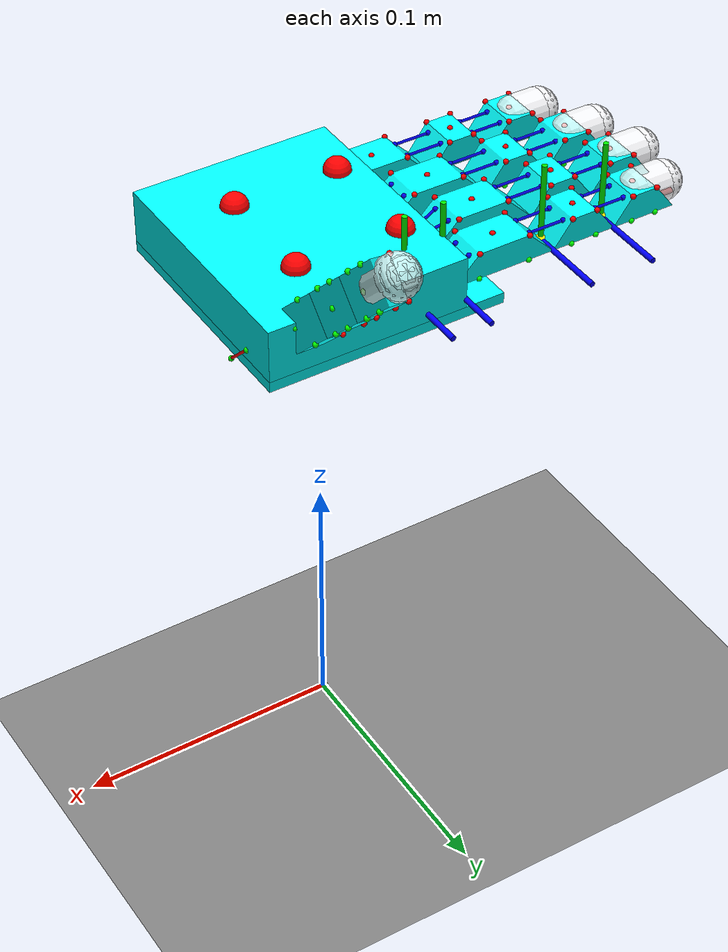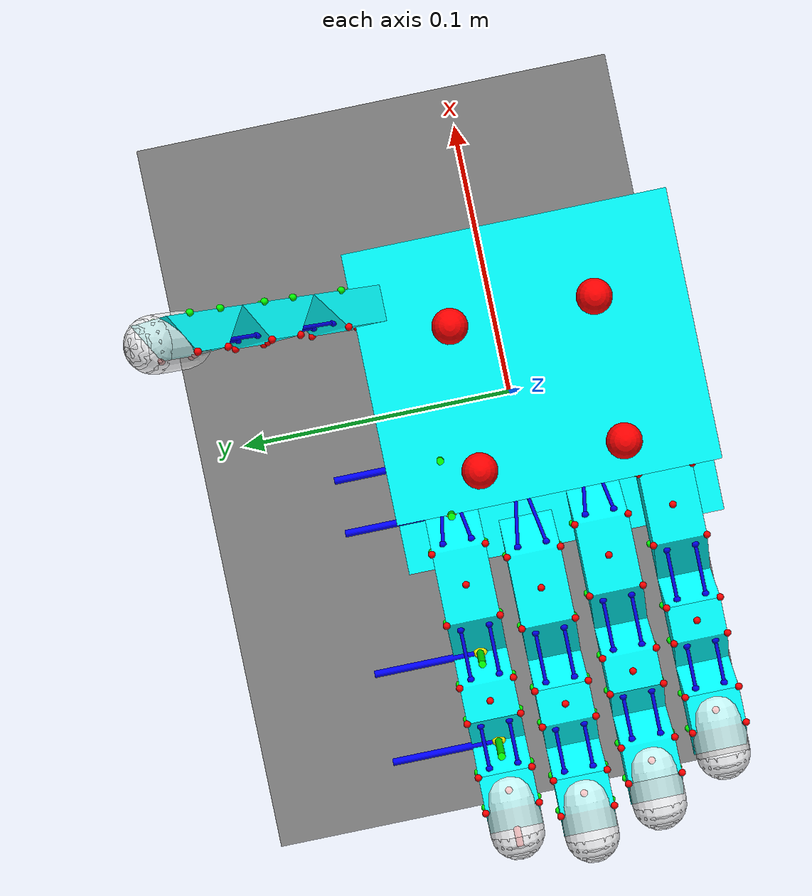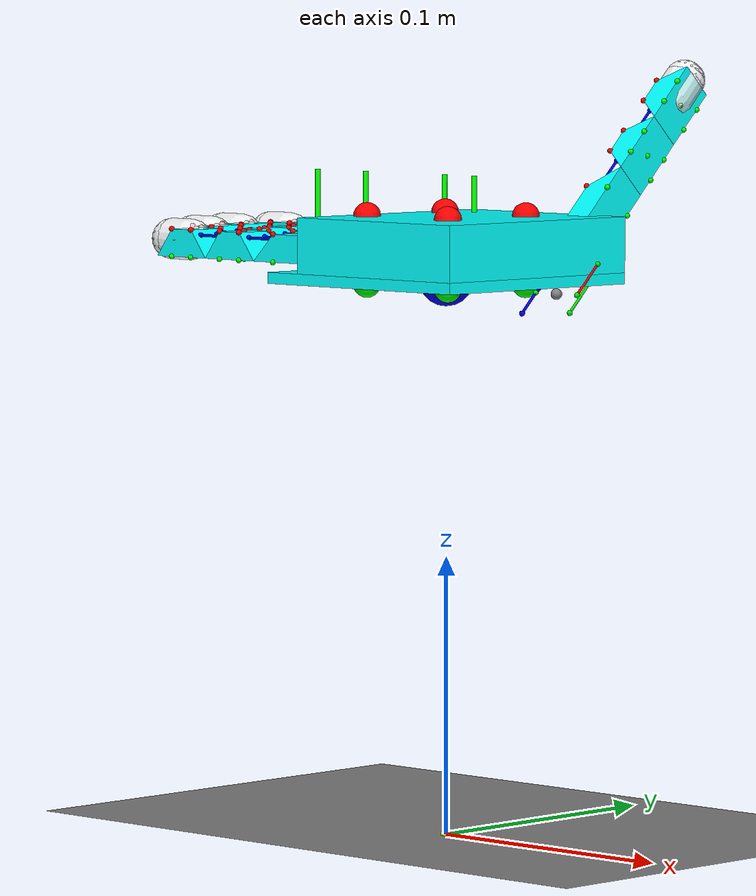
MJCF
<mujoco model="hand">
        <compiler angle="radian" />
        <option integrator="implicitfast"/>
        <!-- TODO： Too large njmax and nconmax may cause problems -->
        <visual>
                <global offwidth="1280" offheight="720"/>
        </visual>
        <asset>
                <mesh name="thumb_base_link" file="./objs/thumb_base_link.obj"/>
                <mesh name="thumb_link_1" file="./objs/thumb_link_1.obj"/>
                <mesh name="thumb_link_2" file="./objs/thumb_link_2.obj"/>
                <mesh name="thumb_link_3" file="./objs/thumb_link_3.obj"/>
                <mesh name="index_base_link" file="./objs/index_base_link.obj"/>
                <mesh name="index_link_1" file="./objs/index_link_1.obj"/>
                <mesh name="index_link_2" file="./objs/index_link_2.obj"/>
                <mesh name="index_link_3" file="./objs/index_link_3.obj"/>
                <mesh name="middle_base_link" file="./objs/middle_base_link.obj"/>
                <mesh name="middle_link_1" file="./objs/middle_link_1.obj"/>
                <mesh name="middle_link_2" file="./objs/middle_link_2.obj"/>
                <mesh name="middle_link_3" file="./objs/middle_link_3.obj"/>
                <mesh name="ring_base_link" file="./objs/ring_base_link.obj"/>
                <mesh name="ring_link_1" file="./objs/ring_link_1.obj"/>
                <mesh name="ring_link_2" file="./objs/ring_link_2.obj"/>
                <mesh name="ring_link_3" file="./objs/ring_link_3.obj"/>
                <mesh name="little_base_link" file="./objs/little_base_link.obj"/>
                <mesh name="little_link_1" file="./objs/little_link_1.obj"/>
                <mesh name="little_link_2" file="./objs/little_link_2.obj"/>
                <mesh name="little_link_3" file="./objs/little_link_3.obj"/>
                <texture type="2d" name="groundplane" builtin="checker" mark="edge" rgb1="1 1 1" rgb2="0 0 0" markrgb="0 0 0" width="300" height="300"/>
                <material name="groundplane" texture="groundplane" texuniform="true" texrepeat="5 5" reflectance="0"/>
        </asset>
        <option gravity="0 0 -9.8"/>
        <default>
                <geom solref="0.001 1" solimp="0.99 0.999 0.0001"/>
        </default>
        <option>
                <flag filterparent ="disable"/>
        </option>
        <contact>
                <exclude body1="palm" body2="thumb_link_1"/>
                <exclude body1="palm" body2="index_link_1"/>
                <exclude body1="palm" body2="middle_link_1"/>
                <exclude body1="palm" body2="ring_link_1"/>
                <exclude body1="palm" body2="little_link_1"/>
        </contact>
        <worldbody>
                <!-- world body frame -->
                <site name="world_frame_origin" type="sphere" size="0.002" rgba="1 1 0 1" pos="0 0 0"/>
                <geom name="world_X" type="cylinder" size="0.001" fromto="0 0 0 0.05 0 0" rgba="1 0 0 1" contype="0" conaffinity="0"/>
                <geom name="world_Y" type="cylinder" size="0.001" fromto="0 0 0 0 0.05 0" rgba="0 1 0 1" contype="0" conaffinity="0"/>
                <geom name="world_Z" type="cylinder" size="0.001" fromto="0 0 0 0 0 0.05" rgba="0 0 1 1" contype="0" conaffinity="0"/>
                <geom name="floor" pos="0 0 0" size="0 0 0.01" type="plane" material="groundplane" contype="1" conaffinity="1" friction="1 0.05 0.05" solref="0.001 1" solimp="0.98 0.99 0.001"/>
                <site name="target" size="0.01" rgba="0 0 .9 1" pos="0 0 .2"/>
                <body name="palm" pos="0 0 0.2" euler="3.14 3.14 0">
                        <joint name="palm_slide_x" type="slide" axis="1 0 0" range="-.5 .5" limited="true" solreflimit=".001 1" solimplimit="0.97 0.99 0.00001 0.1 2" damping="0.2"/>
                        <joint name="palm_slide_y" type="slide" axis="0 1 0" range="-.5 .5" limited="true" solreflimit=".001 1" solimplimit="0.97 0.99 0.00001 0.1 2" damping="0.2"/>
                        <joint name="palm_slide_z" type="slide" axis="0 0 1" range="-.2 .12" limited="true" solreflimit=".001 1" solimplimit="0.97 0.99 0.00001 0.1 2" damping="0.2"/>
                        <joint name="palm_rotate_x" type="hinge" axis="1 0 0" range="-1.57 1.57" limited="true" solreflimit=".001 1" solimplimit="0.97 0.99 0.00001 0.1 2" damping="0.2"/>
                        <joint name="palm_rotate_y" type="hinge" axis="0 1 0" range="-1.57 1.57" limited="true" solreflimit=".001 1" solimplimit="0.97 0.99 0.00001 0.1 2" damping="0.2"/>
                        <joint name="palm_rotate_z" type="hinge" axis="0 0 1" range="-3.14 3.14" limited="true" solreflimit=".001 1" solimplimit="0.97 0.99 0.00001 0.1 2" damping="0.2"/>
                        <geom type="box" size="0.045 0.045 0.002" rgba="0 1 1 1" density="200"/>
                        <geom type="box" size="0.0375 0.045 0.01" pos="-0.0075 0 0.012" rgba="0 1 1 1" density="200"/>
                        <site name="inner_palm_1" size="0.005" rgba="1 0 0 1" pos=".02 .02 0.022"/>
                        <site name="inner_palm_2" size="0.005" rgba="1 0 0 1" pos=".02 -.02 0.022"/>
                        <site name="inner_palm_3" size="0.005" rgba="1 0 0 1" pos="-.02 .02 0.022"/>
                        <site name="inner_palm_4" size="0.005" rgba="1 0 0 1" pos="-.02 -.02 0.022"/>
                        <site name="outer_palm_1" size="0.005" rgba="0 1 0 1" pos=".02 .02 -0.002"/>
                        <site name="outer_palm_2" size="0.005" rgba="0 1 0 1" pos=".02 -.02 -0.002"/>
                        <site name="outer_palm_3" size="0.005" rgba="0 1 0 1" pos="-.02 .02 -0.002"/>
                        <site name="outer_palm_4" size="0.005" rgba="0 1 0 1" pos="-.02 -.02 -0.002"/>
                        <body name="thumb_base_link" pos="-0.035 -0.02 -0.005" euler="-0.785 0 -1.57">
                                <geom conaffinity="0" contype="0" type="sphere" size=".002"/>
                                <site name="thumb_ty_1_1" pos="0 0 0.01" size="0.001" rgba="0 0.9 0 1"/>
                                <site name="thumb_ty_2_1" pos="0 0 -0.01" size="0.001" rgba="0 0.9 0 1"/>
                                <site name="thumb_tx_1_1" pos="0 0.01 0" size="0.001" rgba="0 0.9 0 1"/>
                                <site name="thumb_tx_2_1" pos="0 -0.01 0" size="0.001" rgba="0 0.9 0 1"/>
                                <site name="thumb_t12" pos="0 0.01 0" size="0.001" rgba="0 0 0.9 1"/>
                                <site name="thumb_t0" pos="-0.01 0.01 0" size="0.001" rgba="0 0 0.9 1"/>
                                <body name="thumb_link_1" pos="0.015 0 0">
                                        <joint name="thumb_universal_1" pos="0 0 0" axis="0 0 1" damping="0.1"/>
                                        <joint name="thumb_universal_2" pos="0 0 0" axis="0 1 0" damping="0.1"/>
                                        <geom type="box" pos="0.02 0.005 0" size="0.01 0.005 0.0075" name="thumb_link_1_box_center" density="200" rgba="0 0 1 0"/>
                                        <geom type="box" pos="0.03358578654972743 0.004999436911938167 0" size="0.0060674574081405145 0.001 0.0075" euler="0 0 -0.785" name="thumb_link_1_box_slope1" density="200" rgba="0 0 1 0"/>
                                        <geom type="box" pos="0.006414213450272566 0.005000563088061833 0" size="0.0060674574081405145 0.001 0.0075" euler="0 0 0.785" name="thumb_link_1_box_slope2" density="200" rgba="0 0 1 0"/>
                                        <geom type="box" pos="0.02 0.001 0" size="0.018000000000000002 0.001 0.0075" euler="0 0 0" name="thumb_link_1_box_bottom" density="200" rgba="0 0 1 0"/>
                                        <site name="inner_thumb_1_0" size="0.001" rgba="1 0 0 1" pos="0.02 0.01 0"/>
                                        <site name="inner_thumb_1_1" size="0.001" rgba="1 0 0 1" pos="0.01 0.01 0.0075"/>
                                        <site name="inner_thumb_1_2" size="0.001" rgba="1 0 0 1" pos="0.01 0.01 -0.0075"/>
                                        <site name="inner_thumb_1_3" size="0.001" rgba="1 0 0 1" pos="0.03 0.01 0.0075"/>
                                        <site name="inner_thumb_1_4" size="0.001" rgba="1 0 0 1" pos="0.03 0.01 -0.0075"/>
                                        <site name="outer_thumb_1_0" size="0.001" rgba="0 1 0 1" pos="0.02 0 0"/>
                                        <site name="outer_thumb_1_1" size="0.001" rgba="0 1 0 1" pos="0.01 0 0.0075"/>
                                        <site name="outer_thumb_1_2" size="0.001" rgba="0 1 0 1" pos="0.01 0 -0.0075"/>
                                        <site name="outer_thumb_1_3" size="0.001" rgba="0 1 0 1" pos="0.03 0 0.0075"/>
                                        <site name="outer_thumb_1_4" size="0.001" rgba="0 1 0 1" pos="0.03 0 -0.0075"/>
                                        <geom conaffinity="0" contype="0" type="mesh" rgba="0 1 1 1" mesh="thumb_link_1"/>
                                        <site name="thumb_ty_1_2" pos="0 0 0.01" size="0.001" rgba="0 0.9 0 1"/>
                                        <site name="thumb_ty_2_2" pos="0 0 -0.01" size="0.001" rgba="0 0.9 0 1"/>
                                        <site name="thumb_tx_1_2" pos="0 0.01 0" size="0.001" rgba="0 0.9 0 1"/>
                                        <site name="thumb_tx_2_2" pos="0 -0.01 0" size="0.001" rgba="0 0.9 0 1"/>
                                        <site name="thumb_t1_1_1" pos="0.008 0.008 0.004" size="0.001" rgba="0 0 0.9 1"/>
                                        <site name="thumb_t2_1_1" pos="0.008 0.008 -0.004" size="0.001" rgba="0 0 0.9 1"/>
                                        <site name="thumb_t1_1_2" pos="0.032 0.008 0.004" size="0.001" rgba="0 0 0.9 1"/>
                                        <site name="thumb_t2_1_2" pos="0.032 0.008 -0.004" size="0.001" rgba="0 0 0.9 1"/>
                                        <body name="thumb_link_2" pos="0.04 0 0">
                                                <joint name="thumb_joint_1" pos="0 0 0" axis="0 0 1" stiffness="0.1" springref="0.0" damping="0.2" range="0 1.3" limited="true" solreflimit=".001 1" solimplimit="0.97 0.99 0.00001 0.1 2"/>
                                                <geom type="box" pos="0.0125 0.005 0" size="0.005 0.005 0.0075" name="thumb_link_2_box_center" density="200" rgba="0 0 1 0"/>
                                                <geom type="box" pos="0.019849544644419077 0.005196786170816701 0" size="0.005477355448802637 0.001 0.0075" euler="0 0 -0.925" name="thumb_link_2_box_slope1" density="200" rgba="0 0 1 0"/>
                                                <geom type="box" pos="0.0051504553555809275 0.004803213829183299 0" size="0.005477355448802637 0.001 0.0075" euler="0 0 0.925" name="thumb_link_2_box_slope2" density="200" rgba="0 0 1 0"/>
                                                <geom type="box" pos="0.0125 0.001 0" size="0.0105 0.001 0.0075" euler="0 0 0" name="thumb_link_2_box_bottom" density="200" rgba="0 0 1 0"/>
                                                <site name="inner_thumb_2_0" size="0.001" rgba="1 0 0 1" pos="0.0125 0.01 0"/>
                                                <site name="inner_thumb_2_1" size="0.001" rgba="1 0 0 1" pos="0.007500000000000001 0.01 0.0075"/>
                                                <site name="inner_thumb_2_2" size="0.001" rgba="1 0 0 1" pos="0.007500000000000001 0.01 -0.0075"/>
                                                <site name="inner_thumb_2_3" size="0.001" rgba="1 0 0 1" pos="0.0175 0.01 0.0075"/>
                                                <site name="inner_thumb_2_4" size="0.001" rgba="1 0 0 1" pos="0.0175 0.01 -0.0075"/>
                                                <site name="outer_thumb_2_0" size="0.001" rgba="0 1 0 1" pos="0.0125 0 0"/>
                                                <site name="outer_thumb_2_1" size="0.001" rgba="0 1 0 1" pos="0.007500000000000001 0 0.0075"/>
                                                <site name="outer_thumb_2_2" size="0.001" rgba="0 1 0 1" pos="0.007500000000000001 0 -0.0075"/>
                                                <site name="outer_thumb_2_3" size="0.001" rgba="0 1 0 1" pos="0.0175 0 0.0075"/>
                                                <site name="outer_thumb_2_4" size="0.001" rgba="0 1 0 1" pos="0.0175 0 -0.0075"/>
                                                <geom conaffinity="0" contype="0" type="mesh" rgba="0 1 1 1" mesh="thumb_link_2"/>
                                                <site name="thumb_t1_2_1" pos="0.006 0.008 0.004" size="0.001" rgba="0 0 0.9 1"/>
                                                <site name="thumb_t2_2_1" pos="0.006 0.008 -0.004" size="0.001" rgba="0 0 0.9 1"/>
                                                <site name="thumb_t1_2_2" pos="0.019000000000000003 0.008 0.004" size="0.001" rgba="0 0 0.9 1"/>
                                                <site name="thumb_t2_2_2" pos="0.019000000000000003 0.008 -0.004" size="0.001" rgba="0 0 0.9 1"/>
                                                <body name="thumb_link_3" pos="0.025 0 0">
                                                        <joint name="thumb_joint_2" pos="0 0 0" axis="0 0 1" stiffness="0.1" springref="0.0" damping="0.2" range="0 1.3" limited="true" solreflimit=".001 1" solimplimit="0.97 0.99 0.00001 0.1 2"/>
                                                        <geom type="box" pos="0.0125 0.005 0" size="0.005 0.005 0.0075" name="thumb_link_3_box_center" density="200" rgba="0 0 1 0"/>
                                                        <geom type="box" pos="0.0051504553555809275 0.004803213829183299 0" size="0.005477355448802637 0.001 0.0075" euler="0 0 0.925" name="thumb_link_3_box_slope2" density="200" rgba="0 0 1 0"/>
                                                        <site name="inner_thumb_3_0" size="0.001" rgba="1 0 0 1" pos="0.0125 0.01 0"/>
                                                        <site name="inner_thumb_3_1" size="0.001" rgba="1 0 0 1" pos="0.007500000000000001 0.01 0.0075"/>
                                                        <site name="inner_thumb_3_2" size="0.001" rgba="1 0 0 1" pos="0.007500000000000001 0.01 -0.0075"/>
                                                        <site name="inner_thumb_3_3" size="0.001" rgba="1 0 0 1" pos="0.0175 0.01 0.0075"/>
                                                        <site name="inner_thumb_3_4" size="0.001" rgba="1 0 0 1" pos="0.0175 0.01 -0.0075"/>
                                                        <site name="outer_thumb_3_0" size="0.001" rgba="0 1 0 1" pos="0.0125 0 0"/>
                                                        <site name="outer_thumb_3_1" size="0.001" rgba="0 1 0 1" pos="0.007500000000000001 0 0.0075"/>
                                                        <site name="outer_thumb_3_2" size="0.001" rgba="0 1 0 1" pos="0.007500000000000001 0 -0.0075"/>
                                                        <site name="outer_thumb_3_3" size="0.001" rgba="0 1 0 1" pos="0.0175 0 0.0075"/>
                                                        <site name="outer_thumb_3_4" size="0.001" rgba="0 1 0 1" pos="0.0175 0 -0.0075"/>
                                                        <geom type="sphere" pos="0.025 0.006 0" size="0.0075" rgba="1 1 1 .8" density="200" friction="5 0.5 0.05" />
                                                        <geom type="capsule" euler="0 1.57 0" pos="0.02 0.006 0" size="0.0075 0.005000000000000001" rgba="1 1 1 .8" density="200" friction="5 0.5 0.05" />
                                                        <geom conaffinity="0" contype="0" type="mesh" rgba="0 1 1 1" mesh="thumb_link_3"/>
                                                        <site name="thumb_t1_3" pos="0.006 0.008 0.004" size="0.001" rgba="0 0 0.9 1"/>
                                                        <site name="thumb_t2_3" pos="0.006 0.008 -0.004" size="0.001" rgba="0 0 0.9 1"/>
                                                        <body name="thumb_fingertip" pos="0.02 0.01 0 " euler="1.57 0 0">
                                                                <geom conaffinity="0" contype="0" type="sphere" pos="0 0 0" size=".001" rgba=".9 0 0 .1"/>
                                                                <!--这里插入tactile-->
                                                        </body>
                                                </body>
                                        </body>
                                </body>
                        </body>
                        <body name="index_base_link" pos="0.015 -0.03 0.005" euler="1.57 0 0">
                                <joint name="index_swing" axis="0 -1 0" range="0 0.5" limited="true" solreflimit=".001 1" solimplimit="0.97 0.99 0.00001 0.1 2" damping="0.2"/>
                                <geom conaffinity="0" contype="0" type="sphere" size=".002"/>
                                <site name="index_t12" pos="0 0 0" size="0.001" rgba="0 0 0.9 1"/>
                                <site name="index_t0" pos="-0.01 0 0" size="0.001" rgba="0 0 0.9 1"/>
                                <!-- visable xyz frames -->
                                <site name="index_base_link_frame_origin" type="sphere" size="0.002" rgba="1 1 0 1" pos="0 0 0"/>
                                <geom name="index_base_link_X" type="cylinder" size="0.001" fromto="0 0 0 0.03 0 0" rgba="1 0 0 1" contype="0" conaffinity="0"/>
                                <geom name="index_base_link_Y" type="cylinder" size="0.001" fromto="0 0 0 0 0.03 0" rgba="0 1 0 1" contype="0" conaffinity="0"/>
                                <geom name="index_base_link_Z" type="cylinder" size="0.001" fromto="0 0 0 0 0 0.03" rgba="0 0 1 1" contype="0" conaffinity="0"/>
                                <body name="index_link_1" pos="0.015 0 0">
                                        <joint name="index_joint_0" pos="0 0 0" axis="0 0 1" stiffness="0.6" springref="0.0" damping="0.2" range="0 0.7" limited="true" solreflimit=".001 1" solimplimit="0.97 0.99 0.00001 0.1 2"/>
                                        <!-- visable xyz frames -->
                                        <site name="index_link_1_frame_origin" type="sphere" size="0.002" rgba="1 1 0 1" pos="0 0 0"/>
                                        <geom name="index_link1_X" type="cylinder" size="0.001" fromto="0 0 0 0.03 0 0" rgba="1 0 0 1" contype="0" conaffinity="0"/>
                                        <geom name="index_link1_Y" type="cylinder" size="0.001" fromto="0 0 0 0 0.03 0" rgba="0 1 0 1" contype="0" conaffinity="0"/>
                                        <geom name="index_link1_Z" type="cylinder" size="0.001" fromto="0 0 0 0 0 0.03" rgba="0 0 1 1" contype="0" conaffinity="0"/>
                                        <geom type="box" pos="0.02 0.005 0" size="0.01 0.005 0.0075" name="index_link_1_box_center" density="200" rgba="0 0 1 0"/>
                                        <geom type="box" pos="0.03358578654972743 0.004999436911938167 0" size="0.0060674574081405145 0.001 0.0075" euler="0 0 -0.785" name="index_link_1_box_slope1" density="200" rgba="0 0 1 0"/>
                                        <geom type="box" pos="0.006414213450272566 0.005000563088061833 0" size="0.0060674574081405145 0.001 0.0075" euler="0 0 0.785" name="index_link_1_box_slope2" density="200" rgba="0 0 1 0"/>
                                        <geom type="box" pos="0.02 0.001 0" size="0.018000000000000002 0.001 0.0075" euler="0 0 0" name="index_link_1_box_bottom" density="200" rgba="0 0 1 0"/>

                                        <site name="inner_index_1_0" size="0.001" rgba="1 0 0 1" pos="0.02 0.01 0"/>
                                        <site name="inner_index_1_1" size="0.001" rgba="1 0 0 1" pos="0.01 0.01 0.0075"/>
                                        <site name="inner_index_1_2" size="0.001" rgba="1 0 0 1" pos="0.01 0.01 -0.0075"/>
                                        <site name="inner_index_1_3" size="0.001" rgba="1 0 0 1" pos="0.03 0.01 0.0075"/>
                                        <site name="inner_index_1_4" size="0.001" rgba="1 0 0 1" pos="0.03 0.01 -0.0075"/>
                                        <site name="outer_index_1_0" size="0.001" rgba="0 1 0 1" pos="0.02 0 0"/>
                                        <site name="outer_index_1_1" size="0.001" rgba="0 1 0 1" pos="0.01 0 0.0075"/>
                                        <site name="outer_index_1_2" size="0.001" rgba="0 1 0 1" pos="0.01 0 -0.0075"/>
                                        <site name="outer_index_1_3" size="0.001" rgba="0 1 0 1" pos="0.03 0 0.0075"/>
                                        <site name="outer_index_1_4" size="0.001" rgba="0 1 0 1" pos="0.03 0 -0.0075"/>
                                        <geom conaffinity="0" contype="0" type="mesh" rgba="0 1 1 1" mesh="index_link_1"/>
                                        <site name="index_t1_1_1" pos="0.008 0.008 0.004" size="0.001" rgba="0 0 0.9 1"/>
                                        <site name="index_t2_1_1" pos="0.008 0.008 -0.004" size="0.001" rgba="0 0 0.9 1"/>
                                        <site name="index_t1_1_2" pos="0.032 0.008 0.004" size="0.001" rgba="0 0 0.9 1"/>
                                        <site name="index_t2_1_2" pos="0.032 0.008 -0.004" size="0.001" rgba="0 0 0.9 1"/>
                                        <body name="index_link_2" pos="0.04 0 0">
                                                <joint name="index_joint_1" pos="0 0 0" axis="0 0 1" stiffness="0.4" springref="0.0" damping="0.2" range="0 1.3" limited="true" solreflimit=".001 1" solimplimit="0.97 0.99 0.00001 0.1 2"/>
                                                <!-- visable xyz frames -->
                                                <site name="index_link_2_frame_origin" type="sphere" size="0.002" rgba="1 1 0 1" pos="0 0 0"/>
                                                <geom name="index_link2_X" type="cylinder" size="0.001" fromto="0 0 0 0.03 0 0" rgba="1 0 0 1" contype="0" conaffinity="0"/>
                                                <geom name="index_link2_Y" type="cylinder" size="0.001" fromto="0 0 0 0 0.03 0" rgba="0 1 0 1" contype="0" conaffinity="0"/>
                                                <geom name="index_link2_Z" type="cylinder" size="0.001" fromto="0 0 0 0 0 0.03" rgba="0 0 1 1" contype="0" conaffinity="0"/>
                                                <geom type="box" pos="0.0125 0.005 0" size="0.005 0.005 0.0075" name="index_link_2_box_center" density="200" rgba="0 0 1 0"/>
                                                <geom type="box" pos="0.019849544644419077 0.005196786170816701 0" size="0.005477355448802637 0.001 0.0075" euler="0 0 -0.925" name="index_link_2_box_slope1" density="200" rgba="0 0 1 0"/>
                                                <geom type="box" pos="0.0051504553555809275 0.004803213829183299 0" size="0.005477355448802637 0.001 0.0075" euler="0 0 0.925" name="index_link_2_box_slope2" density="200" rgba="0 0 1 0"/>
                                                <geom type="box" pos="0.0125 0.001 0" size="0.0105 0.001 0.0075" euler="0 0 0" name="index_link_2_box_bottom" density="200" rgba="0 0 1 0"/>
                                                <site name="inner_index_2_0" size="0.001" rgba="1 0 0 1" pos="0.0125 0.01 0"/>
                                                <site name="inner_index_2_1" size="0.001" rgba="1 0 0 1" pos="0.007500000000000001 0.01 0.0075"/>
                                                <site name="inner_index_2_2" size="0.001" rgba="1 0 0 1" pos="0.007500000000000001 0.01 -0.0075"/>
                                                <site name="inner_index_2_3" size="0.001" rgba="1 0 0 1" pos="0.0175 0.01 0.0075"/>
                                                <site name="inner_index_2_4" size="0.001" rgba="1 0 0 1" pos="0.0175 0.01 -0.0075"/>
                                                <site name="outer_index_2_0" size="0.001" rgba="0 1 0 1" pos="0.0125 0 0"/>
                                                <site name="outer_index_2_1" size="0.001" rgba="0 1 0 1" pos="0.007500000000000001 0 0.0075"/>
                                                <site name="outer_index_2_2" size="0.001" rgba="0 1 0 1" pos="0.007500000000000001 0 -0.0075"/>
                                                <site name="outer_index_2_3" size="0.001" rgba="0 1 0 1" pos="0.0175 0 0.0075"/>
                                                <site name="outer_index_2_4" size="0.001" rgba="0 1 0 1" pos="0.0175 0 -0.0075"/>
                                                <geom conaffinity="0" contype="0" type="mesh" rgba="0 1 1 1" mesh="index_link_2"/>
                                                <site name="index_t1_2_1" pos="0.006 0.008 0.004" size="0.001" rgba="0 0 0.9 1"/>
                                                <site name="index_t2_2_1" pos="0.006 0.008 -0.004" size="0.001" rgba="0 0 0.9 1"/>
                                                <site name="index_t1_2_2" pos="0.019000000000000003 0.008 0.004" size="0.001" rgba="0 0 0.9 1"/>
                                                <site name="index_t2_2_2" pos="0.019000000000000003 0.008 -0.004" size="0.001" rgba="0 0 0.9 1"/>
                                                <body name="index_link_3" pos="0.025 0 0">
                                                        <joint name="index_joint_2" pos="0 0 0" axis="0 0 1" stiffness="0.25" springref="0.0" damping="0.2" range="0 1.3" limited="true" solreflimit=".001 1" solimplimit="0.97 0.99 0.00001 0.1 2"/>
                                                        <!-- visable xyz frames -->
                                                        <site name="index_link_3_frame_origin" type="sphere" size="0.002" rgba="1 1 0 1" pos="0 0 0"/>
                                                        <geom name="index_link3_X" type="cylinder" size="0.001" fromto="0 0 0 0.03 0 0" rgba="1 0 0 1" contype="0" conaffinity="0"/>
                                                        <geom name="index_link3_Y" type="cylinder" size="0.001" fromto="0 0 0 0 0.03 0" rgba="0 1 0 1" contype="0" conaffinity="0"/>
                                                        <geom name="index_link3_Z" type="cylinder" size="0.001" fromto="0 0 0 0 0 0.03" rgba="0 0 1 1" contype="0" conaffinity="0"/>
                                                        <geom type="box" pos="0.0125 0.005 0" size="0.005 0.005 0.0075" name="index_link_3_box_center" density="200" rgba="0 0 1 0"/>
                                                        <geom type="box" pos="0.0051504553555809275 0.004803213829183299 0" size="0.005477355448802637 0.001 0.0075" euler="0 0 0.925" name="index_link_3_box_slope2" density="200" rgba="0 0 1 0"/>
                                                        <site name="inner_index_3_0" size="0.001" rgba="1 0 0 1" pos="0.0125 0.01 0"/>
                                                        <site name="inner_index_3_1" size="0.001" rgba="1 0 0 1" pos="0.007500000000000001 0.01 0.0075"/>
                                                        <site name="inner_index_3_2" size="0.001" rgba="1 0 0 1" pos="0.007500000000000001 0.01 -0.0075"/>
                                                        <site name="inner_index_3_3" size="0.001" rgba="1 0 0 1" pos="0.0175 0.01 0.0075"/>
                                                        <site name="inner_index_3_4" size="0.001" rgba="1 0 0 1" pos="0.0175 0.01 -0.0075"/>
                                                        <site name="outer_index_3_0" size="0.001" rgba="0 1 0 1" pos="0.0125 0 0"/>
                                                        <site name="outer_index_3_1" size="0.001" rgba="0 1 0 1" pos="0.007500000000000001 0 0.0075"/>
                                                        <site name="outer_index_3_2" size="0.001" rgba="0 1 0 1" pos="0.007500000000000001 0 -0.0075"/>
                                                        <site name="outer_index_3_3" size="0.001" rgba="0 1 0 1" pos="0.0175 0 0.0075"/>
                                                        <site name="outer_index_3_4" size="0.001" rgba="0 1 0 1" pos="0.0175 0 -0.0075"/>
                                                        <geom type="sphere" pos="0.025 0.006 0" size="0.0075" rgba="1 1 1 .8" density="200" friction="5 0.5 0.05" />
                                                        <geom type="capsule" euler="0 1.57 0" pos="0.02 0.006 0" size="0.0075 0.005000000000000001" rgba="1 1 1 .8" density="200" friction="5 0.5 0.05" />
                                                        <geom conaffinity="0" contype="0" type="mesh" rgba="0 1 1 1" mesh="index_link_3"/>
                                                        <site name="index_t1_3" pos="0.006 0.008 0.004" size="0.001" rgba="0 0 0.9 1"/>
                                                        <site name="index_t2_3" pos="0.006 0.008 -0.004" size="0.001" rgba="0 0 0.9 1"/>
                                                        <body name="index_fingertip" pos="0.02 0.01 0" euler="1.57 0 0">
                                                                <geom conaffinity="0" contype="0" type="sphere" pos="0 0 0" size=".001" rgba=".9 0 0 .1"/>
                                                                <!--这里插入tactile-->
                                                        </body>
                                                </body>
                                        </body>
                                </body>
                        </body>
                        <body name="middle_base_link" pos="0.02 -0.01 0.005" euler="1.57 0 0">
                                <geom conaffinity="0" contype="0" type="sphere" size=".002"/>
                                <site name="middle_t12" pos="0 0 0" size="0.001" rgba="0 0 0.9 1"/>
                                <site name="middle_t0" pos="-0.01 0 0" size="0.001" rgba="0 0 0.9 1"/>
                                <body name="middle_link_1" pos="0.015 0 0">
                                        <joint name="middle_joint_0" pos="0 0 0" axis="0 0 1" stiffness="0.1" springref="0.0" damping="0.2" range="0 0.7" limited="true" solreflimit=".001 1" solimplimit="0.97 0.99 0.00001 0.1 2"/>
                                        <geom type="box" pos="0.02 0.005 0" size="0.01 0.005 0.0075" name="middle_link_1_box_center" density="200" rgba="0 0 1 0"/>
                                        <geom type="box" pos="0.03358578654972743 0.004999436911938167 0" size="0.0060674574081405145 0.001 0.0075" euler="0 0 -0.785" name="middle_link_1_box_slope1" density="200" rgba="0 0 1 0"/>
                                        <geom type="box" pos="0.006414213450272566 0.005000563088061833 0" size="0.0060674574081405145 0.001 0.0075" euler="0 0 0.785" name="middle_link_1_box_slope2" density="200" rgba="0 0 1 0"/>
                                        <geom type="box" pos="0.02 0.001 0" size="0.018000000000000002 0.001 0.0075" euler="0 0 0" name="middle_link_1_box_bottom" density="200" rgba="0 0 1 0"/>
                                        <site name="inner_middle_1_0" size="0.001" rgba="1 0 0 1" pos="0.02 0.01 0"/>
                                        <site name="inner_middle_1_1" size="0.001" rgba="1 0 0 1" pos="0.01 0.01 0.0075"/>
                                        <site name="inner_middle_1_2" size="0.001" rgba="1 0 0 1" pos="0.01 0.01 -0.0075"/>
                                        <site name="inner_middle_1_3" size="0.001" rgba="1 0 0 1" pos="0.03 0.01 0.0075"/>
                                        <site name="inner_middle_1_4" size="0.001" rgba="1 0 0 1" pos="0.03 0.01 -0.0075"/>
                                        <site name="outer_middle_1_0" size="0.001" rgba="0 1 0 1" pos="0.02 0 0"/>
                                        <site name="outer_middle_1_1" size="0.001" rgba="0 1 0 1" pos="0.01 0 0.0075"/>
                                        <site name="outer_middle_1_2" size="0.001" rgba="0 1 0 1" pos="0.01 0 -0.0075"/>
                                        <site name="outer_middle_1_3" size="0.001" rgba="0 1 0 1" pos="0.03 0 0.0075"/>
                                        <site name="outer_middle_1_4" size="0.001" rgba="0 1 0 1" pos="0.03 0 -0.0075"/>
                                        <geom conaffinity="0" contype="0" type="mesh" rgba="0 1 1 1" mesh="middle_link_1"/>
                                        <site name="middle_t1_1_1" pos="0.008 0.008 0.004" size="0.001" rgba="0 0 0.9 1"/>
                                        <site name="middle_t2_1_1" pos="0.008 0.008 -0.004" size="0.001" rgba="0 0 0.9 1"/>
                                        <site name="middle_t1_1_2" pos="0.032 0.008 0.004" size="0.001" rgba="0 0 0.9 1"/>
                                        <site name="middle_t2_1_2" pos="0.032 0.008 -0.004" size="0.001" rgba="0 0 0.9 1"/>
                                        <body name="middle_link_2" pos="0.04 0 0">
                                                <joint name="middle_joint_1" pos="0 0 0" axis="0 0 1" stiffness="0.1" springref="0.0" damping="0.2" range="0 1.3" limited="true" solreflimit=".001 1" solimplimit="0.97 0.99 0.00001 0.1 2"/>
                                                <geom type="box" pos="0.0125 0.005 0" size="0.005 0.005 0.0075" name="middle_link_2_box_center" density="200" rgba="0 0 1 0"/>
                                                <geom type="box" pos="0.019849544644419077 0.005196786170816701 0" size="0.005477355448802637 0.001 0.0075" euler="0 0 -0.925" name="middle_link_2_box_slope1" density="200" rgba="0 0 1 0"/>
                                                <geom type="box" pos="0.0051504553555809275 0.004803213829183299 0" size="0.005477355448802637 0.001 0.0075" euler="0 0 0.925" name="middle_link_2_box_slope2" density="200" rgba="0 0 1 0"/>
                                                <geom type="box" pos="0.0125 0.001 0" size="0.0105 0.001 0.0075" euler="0 0 0" name="middle_link_2_box_bottom" density="200" rgba="0 0 1 0"/>
                                                <site name="inner_middle_2_0" size="0.001" rgba="1 0 0 1" pos="0.0125 0.01 0"/>
                                                <site name="inner_middle_2_1" size="0.001" rgba="1 0 0 1" pos="0.007500000000000001 0.01 0.0075"/>
                                                <site name="inner_middle_2_2" size="0.001" rgba="1 0 0 1" pos="0.007500000000000001 0.01 -0.0075"/>
                                                <site name="inner_middle_2_3" size="0.001" rgba="1 0 0 1" pos="0.0175 0.01 0.0075"/>
                                                <site name="inner_middle_2_4" size="0.001" rgba="1 0 0 1" pos="0.0175 0.01 -0.0075"/>
                                                <site name="outer_middle_2_0" size="0.001" rgba="0 1 0 1" pos="0.0125 0 0"/>
                                                <site name="outer_middle_2_1" size="0.001" rgba="0 1 0 1" pos="0.007500000000000001 0 0.0075"/>
                                                <site name="outer_middle_2_2" size="0.001" rgba="0 1 0 1" pos="0.007500000000000001 0 -0.0075"/>
                                                <site name="outer_middle_2_3" size="0.001" rgba="0 1 0 1" pos="0.0175 0 0.0075"/>
                                                <site name="outer_middle_2_4" size="0.001" rgba="0 1 0 1" pos="0.0175 0 -0.0075"/>
                                                <geom conaffinity="0" contype="0" type="mesh" rgba="0 1 1 1" mesh="middle_link_2"/>
                                                <site name="middle_t1_2_1" pos="0.006 0.008 0.004" size="0.001" rgba="0 0 0.9 1"/>
                                                <site name="middle_t2_2_1" pos="0.006 0.008 -0.004" size="0.001" rgba="0 0 0.9 1"/>
                                                <site name="middle_t1_2_2" pos="0.019000000000000003 0.008 0.004" size="0.001" rgba="0 0 0.9 1"/>
                                                <site name="middle_t2_2_2" pos="0.019000000000000003 0.008 -0.004" size="0.001" rgba="0 0 0.9 1"/>
                                                <body name="middle_link_3" pos="0.025 0 0">
                                                        <joint name="middle_joint_2" pos="0 0 0" axis="0 0 1" stiffness="0.1" springref="0.0" damping="0.2" range="0 1.3" limited="true" solreflimit=".001 1" solimplimit="0.97 0.99 0.00001 0.1 2"/>
                                                        <geom type="box" pos="0.0125 0.005 0" size="0.005 0.005 0.0075" name="middle_link_3_box_center" density="200" rgba="0 0 1 0"/>
                                                        <geom type="box" pos="0.0051504553555809275 0.004803213829183299 0" size="0.005477355448802637 0.001 0.0075" euler="0 0 0.925" name="middle_link_3_box_slope2" density="200" rgba="0 0 1 0"/>
                                                        <site name="inner_middle_3_0" size="0.001" rgba="1 0 0 1" pos="0.0125 0.01 0"/>
                                                        <site name="inner_middle_3_1" size="0.001" rgba="1 0 0 1" pos="0.007500000000000001 0.01 0.0075"/>
                                                        <site name="inner_middle_3_2" size="0.001" rgba="1 0 0 1" pos="0.007500000000000001 0.01 -0.0075"/>
                                                        <site name="inner_middle_3_3" size="0.001" rgba="1 0 0 1" pos="0.0175 0.01 0.0075"/>
                                                        <site name="inner_middle_3_4" size="0.001" rgba="1 0 0 1" pos="0.0175 0.01 -0.0075"/>
                                                        <site name="outer_middle_3_0" size="0.001" rgba="0 1 0 1" pos="0.0125 0 0"/>
                                                        <site name="outer_middle_3_1" size="0.001" rgba="0 1 0 1" pos="0.007500000000000001 0 0.0075"/>
                                                        <site name="outer_middle_3_2" size="0.001" rgba="0 1 0 1" pos="0.007500000000000001 0 -0.0075"/>
                                                        <site name="outer_middle_3_3" size="0.001" rgba="0 1 0 1" pos="0.0175 0 0.0075"/>
                                                        <site name="outer_middle_3_4" size="0.001" rgba="0 1 0 1" pos="0.0175 0 -0.0075"/>
                                                        <geom type="sphere" pos="0.025 0.006 0" size="0.0075" rgba="1 1 1 .8" density="200" friction="5 0.5 0.05" />
                                                        <geom type="capsule" euler="0 1.57 0" pos="0.02 0.006 0" size="0.0075 0.005000000000000001" rgba="1 1 1 .8" density="200" friction="5 0.5 0.05" />
                                                        <geom conaffinity="0" contype="0" type="mesh" rgba="0 1 1 1" mesh="middle_link_3"/>
                                                        <site name="middle_t1_3" pos="0.006 0.008 0.004" size="0.001" rgba="0 0 0.9 1"/>
                                                        <site name="middle_t2_3" pos="0.006 0.008 -0.004" size="0.001" rgba="0 0 0.9 1"/>
                                                        <body name="middle_fingertip" pos="0.02 0.01 0" euler="1.57 0 0">
                                                                <geom conaffinity="0" contype="0" type="sphere" pos="0 0 0" size=".001" rgba=".9 0 0 .1"/>
                                                                <!--这里插入tactile-->
                                                        </body>
                                                </body>
                                        </body>
                                </body>
                        </body>
                        <body name="ring_base_link" pos="0.015 0.01 0.005" euler="1.57 0 0">
                                <joint name="ring_swing" axis="0 1 0" range="0 0.5" limited="true" solreflimit=".001 1" solimplimit="0.97 0.99 0.00001 0.1 2" damping="0.2"/>
                                <geom conaffinity="0" contype="0" type="sphere" size=".002"/>
                                <site name="ring_t12" pos="0 0 0" size="0.001" rgba="0 0 0.9 1"/>
                                <site name="ring_t0" pos="-0.01 0 0" size="0.001" rgba="0 0 0.9 1"/>
                                <body name="ring_link_1" pos="0.015 0 0">
                                        <joint name="ring_joint_0" pos="0 0 0" axis="0 0 1" stiffness="0.1" springref="0.0" damping="0.2" range="0 0.7" limited="true" solreflimit=".001 1" solimplimit="0.97 0.99 0.00001 0.1 2"/>
                                        <geom type="box" pos="0.02 0.005 0" size="0.01 0.005 0.0075" name="ring_link_1_box_center" density="200" rgba="0 0 1 0"/>
                                        <geom type="box" pos="0.03358578654972743 0.004999436911938167 0" size="0.0060674574081405145 0.001 0.0075" euler="0 0 -0.785" name="ring_link_1_box_slope1" density="200" rgba="0 0 1 0"/>
                                        <geom type="box" pos="0.006414213450272566 0.005000563088061833 0" size="0.0060674574081405145 0.001 0.0075" euler="0 0 0.785" name="ring_link_1_box_slope2" density="200" rgba="0 0 1 0"/>
                                        <geom type="box" pos="0.02 0.001 0" size="0.018000000000000002 0.001 0.0075" euler="0 0 0" name="ring_link_1_box_bottom" density="200" rgba="0 0 1 0"/>
                                        <site name="inner_ring_1_0" size="0.001" rgba="1 0 0 1" pos="0.02 0.01 0"/>
                                        <site name="inner_ring_1_1" size="0.001" rgba="1 0 0 1" pos="0.01 0.01 0.0075"/>
                                        <site name="inner_ring_1_2" size="0.001" rgba="1 0 0 1" pos="0.01 0.01 -0.0075"/>
                                        <site name="inner_ring_1_3" size="0.001" rgba="1 0 0 1" pos="0.03 0.01 0.0075"/>
                                        <site name="inner_ring_1_4" size="0.001" rgba="1 0 0 1" pos="0.03 0.01 -0.0075"/>
                                        <site name="outer_ring_1_0" size="0.001" rgba="0 1 0 1" pos="0.02 0 0"/>
                                        <site name="outer_ring_1_1" size="0.001" rgba="0 1 0 1" pos="0.01 0 0.0075"/>
                                        <site name="outer_ring_1_2" size="0.001" rgba="0 1 0 1" pos="0.01 0 -0.0075"/>
                                        <site name="outer_ring_1_3" size="0.001" rgba="0 1 0 1" pos="0.03 0 0.0075"/>
                                        <site name="outer_ring_1_4" size="0.001" rgba="0 1 0 1" pos="0.03 0 -0.0075"/>
                                        <geom conaffinity="0" contype="0" type="mesh" rgba="0 1 1 1" mesh="ring_link_1"/>
                                        <site name="ring_t1_1_1" pos="0.008 0.008 0.004" size="0.001" rgba="0 0 0.9 1"/>
                                        <site name="ring_t2_1_1" pos="0.008 0.008 -0.004" size="0.001" rgba="0 0 0.9 1"/>
                                        <site name="ring_t1_1_2" pos="0.032 0.008 0.004" size="0.001" rgba="0 0 0.9 1"/>
                                        <site name="ring_t2_1_2" pos="0.032 0.008 -0.004" size="0.001" rgba="0 0 0.9 1"/>
                                        <body name="ring_link_2" pos="0.04 0 0">
                                                <joint name="ring_joint_1" pos="0 0 0" axis="0 0 1" stiffness="0.1" springref="0.0" damping="0.2" range="0 1.3" limited="true" solreflimit=".001 1" solimplimit="0.97 0.99 0.00001 0.1 2"/>
                                                <geom type="box" pos="0.0125 0.005 0" size="0.005 0.005 0.0075" name="ring_link_2_box_center" density="200" rgba="0 0 1 0"/>
                                                <geom type="box" pos="0.019849544644419077 0.005196786170816701 0" size="0.005477355448802637 0.001 0.0075" euler="0 0 -0.925" name="ring_link_2_box_slope1" density="200" rgba="0 0 1 0"/>
                                                <geom type="box" pos="0.0051504553555809275 0.004803213829183299 0" size="0.005477355448802637 0.001 0.0075" euler="0 0 0.925" name="ring_link_2_box_slope2" density="200" rgba="0 0 1 0"/>
                                                <geom type="box" pos="0.0125 0.001 0" size="0.0105 0.001 0.0075" euler="0 0 0" name="ring_link_2_box_bottom" density="200" rgba="0 0 1 0"/>
                                                <site name="inner_ring_2_0" size="0.001" rgba="1 0 0 1" pos="0.0125 0.01 0"/>
                                                <site name="inner_ring_2_1" size="0.001" rgba="1 0 0 1" pos="0.007500000000000001 0.01 0.0075"/>
                                                <site name="inner_ring_2_2" size="0.001" rgba="1 0 0 1" pos="0.007500000000000001 0.01 -0.0075"/>
                                                <site name="inner_ring_2_3" size="0.001" rgba="1 0 0 1" pos="0.0175 0.01 0.0075"/>
                                                <site name="inner_ring_2_4" size="0.001" rgba="1 0 0 1" pos="0.0175 0.01 -0.0075"/>
                                                <site name="outer_ring_2_0" size="0.001" rgba="0 1 0 1" pos="0.0125 0 0"/>
                                                <site name="outer_ring_2_1" size="0.001" rgba="0 1 0 1" pos="0.007500000000000001 0 0.0075"/>
                                                <site name="outer_ring_2_2" size="0.001" rgba="0 1 0 1" pos="0.007500000000000001 0 -0.0075"/>
                                                <site name="outer_ring_2_3" size="0.001" rgba="0 1 0 1" pos="0.0175 0 0.0075"/>
                                                <site name="outer_ring_2_4" size="0.001" rgba="0 1 0 1" pos="0.0175 0 -0.0075"/>
                                                <geom conaffinity="0" contype="0" type="mesh" rgba="0 1 1 1" mesh="ring_link_2"/>
                                                <site name="ring_t1_2_1" pos="0.006 0.008 0.004" size="0.001" rgba="0 0 0.9 1"/>
                                                <site name="ring_t2_2_1" pos="0.006 0.008 -0.004" size="0.001" rgba="0 0 0.9 1"/>
                                                <site name="ring_t1_2_2" pos="0.019000000000000003 0.008 0.004" size="0.001" rgba="0 0 0.9 1"/>
                                                <site name="ring_t2_2_2" pos="0.019000000000000003 0.008 -0.004" size="0.001" rgba="0 0 0.9 1"/>
                                                <body name="ring_link_3" pos="0.025 0 0">
                                                        <joint name="ring_joint_2" pos="0 0 0" axis="0 0 1" stiffness="0.1" springref="0.0" damping="0.2" range="0 1.3" limited="true" solreflimit=".001 1" solimplimit="0.97 0.99 0.00001 0.1 2"/>
                                                        <geom type="box" pos="0.0125 0.005 0" size="0.005 0.005 0.0075" name="ring_link_3_box_center" density="200" rgba="0 0 1 0"/>
                                                        <geom type="box" pos="0.0051504553555809275 0.004803213829183299 0" size="0.005477355448802637 0.001 0.0075" euler="0 0 0.925" name="ring_link_3_box_slope2" density="200" rgba="0 0 1 0"/>
                                                        <site name="inner_ring_3_0" size="0.001" rgba="1 0 0 1" pos="0.0125 0.01 0"/>
                                                        <site name="inner_ring_3_1" size="0.001" rgba="1 0 0 1" pos="0.007500000000000001 0.01 0.0075"/>
                                                        <site name="inner_ring_3_2" size="0.001" rgba="1 0 0 1" pos="0.007500000000000001 0.01 -0.0075"/>
                                                        <site name="inner_ring_3_3" size="0.001" rgba="1 0 0 1" pos="0.0175 0.01 0.0075"/>
                                                        <site name="inner_ring_3_4" size="0.001" rgba="1 0 0 1" pos="0.0175 0.01 -0.0075"/>
                                                        <site name="outer_ring_3_0" size="0.001" rgba="0 1 0 1" pos="0.0125 0 0"/>
                                                        <site name="outer_ring_3_1" size="0.001" rgba="0 1 0 1" pos="0.007500000000000001 0 0.0075"/>
                                                        <site name="outer_ring_3_2" size="0.001" rgba="0 1 0 1" pos="0.007500000000000001 0 -0.0075"/>
                                                        <site name="outer_ring_3_3" size="0.001" rgba="0 1 0 1" pos="0.0175 0 0.0075"/>
                                                        <site name="outer_ring_3_4" size="0.001" rgba="0 1 0 1" pos="0.0175 0 -0.0075"/>
                                                        <geom type="sphere" pos="0.025 0.006 0" size="0.0075" rgba="1 1 1 .8" density="200" friction="5 0.5 0.05" />
                                                        <geom type="capsule" euler="0 1.57 0" pos="0.02 0.006 0" size="0.0075 0.005000000000000001" rgba="1 1 1 .8" density="200" friction="5 0.5 0.05" />
                                                        <geom conaffinity="0" contype="0" type="mesh" rgba="0 1 1 1" mesh="ring_link_3"/>
                                                        <site name="ring_t1_3" pos="0.006 0.008 0.004" size="0.001" rgba="0 0 0.9 1"/>
                                                        <site name="ring_t2_3" pos="0.006 0.008 -0.004" size="0.001" rgba="0 0 0.9 1"/>
                                                        <body name="ring_fingertip" pos="0.02 0.01 0" euler="1.57 0 0">
                                                                <geom conaffinity="0" contype="0" type="sphere" pos="0 0 0" size=".001" rgba=".9 0 0 .1"/>
                                                                <!--这里插入tactile-->
                                                        </body>
                                                </body>
                                        </body>
                                </body>
                        </body>
                        <body name="little_base_link" pos="0.005 0.03 0.005" euler="1.57 0 0">
                                <joint name="little_swing" axis="0 1 0" range="0 0.75" limited="true" solreflimit=".001 1" solimplimit="0.97 0.99 0.00001 0.1 2" damping="0.2"/>
                                <geom conaffinity="0" contype="0" type="sphere" size=".002"/>
                                <site name="little_t12" pos="0 0 0" size="0.001" rgba="0 0 0.9 1"/>
                                <site name="little_t0" pos="-0.01 0 0" size="0.001" rgba="0 0 0.9 1"/>
                                <body name="little_link_1" pos="0.015 0 0">
                                        <joint name="little_joint_0" pos="0 0 0" axis="0 0 1" stiffness="0.1" springref="0.0" damping="0.2" range="0 0.7" limited="true" solreflimit=".001 1" solimplimit="0.97 0.99 0.00001 0.1 2"/>
                                        <geom type="box" pos="0.02 0.005 0" size="0.01 0.005 0.0075" name="little_link_1_box_center" density="200" rgba="0 0 1 0"/>
                                        <geom type="box" pos="0.03358578654972743 0.004999436911938167 0" size="0.0060674574081405145 0.001 0.0075" euler="0 0 -0.785" name="little_link_1_box_slope1" density="200" rgba="0 0 1 0"/>
                                        <geom type="box" pos="0.006414213450272566 0.005000563088061833 0" size="0.0060674574081405145 0.001 0.0075" euler="0 0 0.785" name="little_link_1_box_slope2" density="200" rgba="0 0 1 0"/>
                                        <geom type="box" pos="0.02 0.001 0" size="0.018000000000000002 0.001 0.0075" euler="0 0 0" name="little_link_1_box_bottom" density="200" rgba="0 0 1 0"/>
                                        <site name="inner_little_1_0" size="0.001" rgba="1 0 0 1" pos="0.02 0.01 0"/>
                                        <site name="inner_little_1_1" size="0.001" rgba="1 0 0 1" pos="0.01 0.01 0.0075"/>
                                        <site name="inner_little_1_2" size="0.001" rgba="1 0 0 1" pos="0.01 0.01 -0.0075"/>
                                        <site name="inner_little_1_3" size="0.001" rgba="1 0 0 1" pos="0.03 0.01 0.0075"/>
                                        <site name="inner_little_1_4" size="0.001" rgba="1 0 0 1" pos="0.03 0.01 -0.0075"/>
                                        <site name="outer_little_1_0" size="0.001" rgba="0 1 0 1" pos="0.02 0 0"/>
                                        <site name="outer_little_1_1" size="0.001" rgba="0 1 0 1" pos="0.01 0 0.0075"/>
                                        <site name="outer_little_1_2" size="0.001" rgba="0 1 0 1" pos="0.01 0 -0.0075"/>
                                        <site name="outer_little_1_3" size="0.001" rgba="0 1 0 1" pos="0.03 0 0.0075"/>
                                        <site name="outer_little_1_4" size="0.001" rgba="0 1 0 1" pos="0.03 0 -0.0075"/>
                                        <geom conaffinity="0" contype="0" type="mesh" rgba="0 1 1 1" mesh="little_link_1"/>
                                        <site name="little_t1_1_1" pos="0.008 0.008 0.004" size="0.001" rgba="0 0 0.9 1"/>
                                        <site name="little_t2_1_1" pos="0.008 0.008 -0.004" size="0.001" rgba="0 0 0.9 1"/>
                                        <site name="little_t1_1_2" pos="0.032 0.008 0.004" size="0.001" rgba="0 0 0.9 1"/>
                                        <site name="little_t2_1_2" pos="0.032 0.008 -0.004" size="0.001" rgba="0 0 0.9 1"/>
                                        <body name="little_link_2" pos="0.04 0 0">
                                                <joint name="little_joint_1" pos="0 0 0" axis="0 0 1" stiffness="0.1" springref="0.0" damping="0.2" range="0 1.3" limited="true" solreflimit=".001 1" solimplimit="0.97 0.99 0.00001 0.1 2"/>
                                                <geom type="box" pos="0.0125 0.005 0" size="0.005 0.005 0.0075" name="little_link_2_box_center" density="200" rgba="0 0 1 0"/>
                                                <geom type="box" pos="0.019849544644419077 0.005196786170816701 0" size="0.005477355448802637 0.001 0.0075" euler="0 0 -0.925" name="little_link_2_box_slope1" density="200" rgba="0 0 1 0"/>
                                                <geom type="box" pos="0.0051504553555809275 0.004803213829183299 0" size="0.005477355448802637 0.001 0.0075" euler="0 0 0.925" name="little_link_2_box_slope2" density="200" rgba="0 0 1 0"/>
                                                <geom type="box" pos="0.0125 0.001 0" size="0.0105 0.001 0.0075" euler="0 0 0" name="little_link_2_box_bottom" density="200" rgba="0 0 1 0"/>
                                                <site name="inner_little_2_0" size="0.001" rgba="1 0 0 1" pos="0.0125 0.01 0"/>
                                                <site name="inner_little_2_1" size="0.001" rgba="1 0 0 1" pos="0.007500000000000001 0.01 0.0075"/>
                                                <site name="inner_little_2_2" size="0.001" rgba="1 0 0 1" pos="0.007500000000000001 0.01 -0.0075"/>
                                                <site name="inner_little_2_3" size="0.001" rgba="1 0 0 1" pos="0.0175 0.01 0.0075"/>
                                                <site name="inner_little_2_4" size="0.001" rgba="1 0 0 1" pos="0.0175 0.01 -0.0075"/>
                                                <site name="outer_little_2_0" size="0.001" rgba="0 1 0 1" pos="0.0125 0 0"/>
                                                <site name="outer_little_2_1" size="0.001" rgba="0 1 0 1" pos="0.007500000000000001 0 0.0075"/>
                                                <site name="outer_little_2_2" size="0.001" rgba="0 1 0 1" pos="0.007500000000000001 0 -0.0075"/>
                                                <site name="outer_little_2_3" size="0.001" rgba="0 1 0 1" pos="0.0175 0 0.0075"/>
                                                <site name="outer_little_2_4" size="0.001" rgba="0 1 0 1" pos="0.0175 0 -0.0075"/>
                                                <geom conaffinity="0" contype="0" type="mesh" rgba="0 1 1 1" mesh="little_link_2"/>
                                                <site name="little_t1_2_1" pos="0.006 0.008 0.004" size="0.001" rgba="0 0 0.9 1"/>
                                                <site name="little_t2_2_1" pos="0.006 0.008 -0.004" size="0.001" rgba="0 0 0.9 1"/>
                                                <site name="little_t1_2_2" pos="0.019000000000000003 0.008 0.004" size="0.001" rgba="0 0 0.9 1"/>
                                                <site name="little_t2_2_2" pos="0.019000000000000003 0.008 -0.004" size="0.001" rgba="0 0 0.9 1"/>
                                                <body name="little_link_3" pos="0.025 0 0">
                                                        <joint name="little_joint_2" pos="0 0 0" axis="0 0 1" stiffness="0.1" springref="0.0" damping="0.2" range="0 1.3" limited="true" solreflimit=".001 1" solimplimit="0.97 0.99 0.00001 0.1 2"/>
                                                        <geom type="box" pos="0.0125 0.005 0" size="0.005 0.005 0.0075" name="little_link_3_box_center" density="200" rgba="0 0 1 0"/>
                                                        <geom type="box" pos="0.0051504553555809275 0.004803213829183299 0" size="0.005477355448802637 0.001 0.0075" euler="0 0 0.925" name="little_link_3_box_slope2" density="200" rgba="0 0 1 0"/>
                                                        <site name="inner_little_3_0" size="0.001" rgba="1 0 0 1" pos="0.0125 0.01 0"/>
                                                        <site name="inner_little_3_1" size="0.001" rgba="1 0 0 1" pos="0.007500000000000001 0.01 0.0075"/>
                                                        <site name="inner_little_3_2" size="0.001" rgba="1 0 0 1" pos="0.007500000000000001 0.01 -0.0075"/>
                                                        <site name="inner_little_3_3" size="0.001" rgba="1 0 0 1" pos="0.0175 0.01 0.0075"/>
                                                        <site name="inner_little_3_4" size="0.001" rgba="1 0 0 1" pos="0.0175 0.01 -0.0075"/>
                                                        <site name="outer_little_3_0" size="0.001" rgba="0 1 0 1" pos="0.0125 0 0"/>
                                                        <site name="outer_little_3_1" size="0.001" rgba="0 1 0 1" pos="0.007500000000000001 0 0.0075"/>
                                                        <site name="outer_little_3_2" size="0.001" rgba="0 1 0 1" pos="0.007500000000000001 0 -0.0075"/>
                                                        <site name="outer_little_3_3" size="0.001" rgba="0 1 0 1" pos="0.0175 0 0.0075"/>
                                                        <site name="outer_little_3_4" size="0.001" rgba="0 1 0 1" pos="0.0175 0 -0.0075"/>
                                                        <geom type="sphere" pos="0.025 0.006 0" size="0.0075" rgba="1 1 1 .8" density="200" friction="5 0.5 0.05" />
                                                        <geom type="capsule" euler="0 1.57 0" pos="0.02 0.006 0" size="0.0075 0.005000000000000001" rgba="1 1 1 .8" density="200" friction="5 0.5 0.05" />
                                                        <geom conaffinity="0" contype="0" type="mesh" rgba="0 1 1 1" mesh="little_link_3"/>
                                                        <site name="little_t1_3" pos="0.006 0.008 0.004" size="0.001" rgba="0 0 0.9 1"/>
                                                        <site name="little_t2_3" pos="0.006 0.008 -0.004" size="0.001" rgba="0 0 0.9 1"/>
                                                        <body name="little_fingertip" pos="0.02 0.01 0" euler="1.57 0 0">
                                                                <geom conaffinity="0" contype="0" type="sphere" pos="0 0 0" size=".001" rgba=".9 0 0 .1"/>
                                                                <!--这里插入tactile-->
                                                        </body>
                                                </body>
                                        </body>
                                </body>
                        </body>
                </body>
        </worldbody>
        <tendon>
                <!-- 定义各绳索，依次连接各节点 -->
                <spatial name="thumb_tendon_x1" width=".0005" rgba=".9 .0 .0 1">
                        <site site="thumb_tx_1_1"/>
                        <site site="thumb_tx_1_2"/>
                </spatial>
                <spatial name="thumb_tendon_x2"  width=".0005" rgba=".9 .0 .0 1">
                        <site site="thumb_tx_2_2"/>
                        <site site="thumb_tx_2_1"/>
                </spatial>
                <spatial name="thumb_tendon_y1"  width=".0005" rgba="0 .9 .0 1">
                        <site site="thumb_ty_1_1"/>
                        <site site="thumb_ty_1_2"/>
                </spatial>
                <spatial name="thumb_tendon_y2"  width=".0005" rgba="0 .9 .0 1">
                        <site site="thumb_ty_2_2"/>
                        <site site="thumb_ty_2_1"/>
                </spatial>
                <!-- 这里的range和limited是限制其长度，solreflimit和solimplimit是用于定义limited的约束强度 -->
                <spatial name="thumb_tendon"  width=".0005" rgba="0 0 .9 1" limited="true" range="0.07043074902771998 0.09643074902771996" solreflimit=".001 1" solimplimit="0.99 0.999 0.00001 0.1 2">
                        <site site="thumb_t0"/>
                        <site site="thumb_t12"/>
                        <!-- 用pulley来将绳索分为两股 -->
                        <pulley divisor="2"/>
                        <site site="thumb_t12"/>
                        <site site="thumb_t1_1_1"/>
                        <site site="thumb_t1_1_2"/>
                        <site site="thumb_t1_2_1"/>
                        <site site="thumb_t1_2_2"/>
                        <site site="thumb_t1_3"/>
                        <!-- 用pulley来将绳索分为两股 -->
                        <pulley divisor="2"/>
                        <site site="thumb_t12"/>
                        <site site="thumb_t2_1_1"/>
                        <site site="thumb_t2_1_2"/>
                        <site site="thumb_t2_2_1"/>
                        <site site="thumb_t2_2_2"/>
                        <site site="thumb_t2_3"/>
                </spatial>
                <!-- 定义各绳索，依次连接各节点 -->
                <!-- 这里的range和limited是限制其长度，solreflimit和solimplimit是用于定义limited的约束强度 -->
                <spatial name="index_tendon"  width=".0005" rgba="0 0 .9 1" limited="true" range="0.07167792535850614 0.09767792535850614" solreflimit=".001 1" solimplimit="0.99 0.999 0.00001 0.1 2">
                        <site site="index_t0"/>
                        <site site="index_t12"/>
                        <!-- 用pulley来将绳索分为两股 -->
                        <pulley divisor="2"/>
                        <site site="index_t12"/>
                        <site site="index_t1_1_1"/>
                        <site site="index_t1_1_2"/>
                        <site site="index_t1_2_1"/>
                        <site site="index_t1_2_2"/>
                        <site site="index_t1_3"/>
                        <!-- 用pulley来将绳索分为两股 -->
                        <pulley divisor="2"/>
                        <site site="index_t12"/>
                        <site site="index_t2_1_1"/>
                        <site site="index_t2_1_2"/>
                        <site site="index_t2_2_1"/>
                        <site site="index_t2_2_2"/>
                        <site site="index_t2_3"/>
                </spatial>
                <!-- 定义各绳索，依次连接各节点 -->
                <!-- 这里的range和limited是限制其长度，solreflimit和solimplimit是用于定义limited的约束强度 -->
                <spatial name="middle_tendon"  width=".0005" rgba="0 0 .9 1" limited="true" range="0.07167792535850614 0.09767792535850614" solreflimit=".001 1" solimplimit="0.99 0.999 0.00001 0.1 2">
                        <site site="middle_t0"/>
                        <site site="middle_t12"/>
                        <!-- 用pulley来将绳索分为两股 -->
                        <pulley divisor="2"/>
                        <site site="middle_t12"/>
                        <site site="middle_t1_1_1"/>
                        <site site="middle_t1_1_2"/>
                        <site site="middle_t1_2_1"/>
                        <site site="middle_t1_2_2"/>
                        <site site="middle_t1_3"/>
                        <!-- 用pulley来将绳索分为两股 -->
                        <pulley divisor="2"/>
                        <site site="middle_t12"/>
                        <site site="middle_t2_1_1"/>
                        <site site="middle_t2_1_2"/>
                        <site site="middle_t2_2_1"/>
                        <site site="middle_t2_2_2"/>
                        <site site="middle_t2_3"/>
                </spatial>
                <!-- 定义各绳索，依次连接各节点 -->
                <!-- 这里的range和limited是限制其长度，solreflimit和solimplimit是用于定义limited的约束强度 -->
                <spatial name="ring_tendon"  width=".0005" rgba="0 0 .9 1" limited="true" range="0.07167792535850614 0.09767792535850614" solreflimit=".001 1" solimplimit="0.99 0.999 0.00001 0.1 2">
                        <site site="ring_t0"/>
                        <site site="ring_t12"/>
                        <!-- 用pulley来将绳索分为两股 -->
                        <pulley divisor="2"/>
                        <site site="ring_t12"/>
                        <site site="ring_t1_1_1"/>
                        <site site="ring_t1_1_2"/>
                        <site site="ring_t1_2_1"/>
                        <site site="ring_t1_2_2"/>
                        <site site="ring_t1_3"/>
                        <!-- 用pulley来将绳索分为两股 -->
                        <pulley divisor="2"/>
                        <site site="ring_t12"/>
                        <site site="ring_t2_1_1"/>
                        <site site="ring_t2_1_2"/>
                        <site site="ring_t2_2_1"/>
                        <site site="ring_t2_2_2"/>
                        <site site="ring_t2_3"/>
                </spatial>
                <!-- 定义各绳索，依次连接各节点 -->
                <!-- 这里的range和limited是限制其长度，solreflimit和solimplimit是用于定义limited的约束强度 -->
                <spatial name="little_tendon"  width=".0005" rgba="0 0 .9 1" limited="true" range="0.07167792535850614 0.09767792535850614" solreflimit=".001 1" solimplimit="0.99 0.999 0.00001 0.1 2">
                        <site site="little_t0"/>
                        <site site="little_t12"/>
                        <!-- 用pulley来将绳索分为两股 -->
                        <pulley divisor="2"/>
                        <site site="little_t12"/>
                        <site site="little_t1_1_1"/>
                        <site site="little_t1_1_2"/>
                        <site site="little_t1_2_1"/>
                        <site site="little_t1_2_2"/>
                        <site site="little_t1_3"/>
                        <!-- 用pulley来将绳索分为两股 -->
                        <pulley divisor="2"/>
                        <site site="little_t12"/>
                        <site site="little_t2_1_1"/>
                        <site site="little_t2_1_2"/>
                        <site site="little_t2_2_1"/>
                        <site site="little_t2_2_2"/>
                        <site site="little_t2_3"/>
                </spatial>
        </tendon>
        <actuator>
                <!-- 定义各个绳索的驱动 -->
                <!-- 弯曲绳索用哑物体控制，驱动安装在哑物体的平动关节上，设置控制范围，以及控制量的Kp（与位移差成正比）与Kv（与速度成正比）指数 -->
                <motor name="thumb_tendon" tendon="thumb_tendon" ctrllimited="true" ctrlrange="-20 0"/>
                <!-- 万向节周边的绳索直接用绳索长度进行控制，驱动安装在绳索上 -->
                <position name="thumb_tendon_x1" tendon="thumb_tendon_x1" forcerange="-50 0" forcelimited="true" ctrllimited="true" ctrlrange=" 0 0.03" kp="10000" dampratio="1.5"/>
                <position name="thumb_tendon_x2" tendon="thumb_tendon_x2" forcerange="-50 0" forcelimited="true" ctrllimited="true" ctrlrange=" 0 0.03" kp="10000" dampratio="1.5"/>
                <position name="thumb_tendon_y1" tendon="thumb_tendon_y1" forcerange="-50 0" forcelimited="true" ctrllimited="true" ctrlrange=" 0 0.03" kp="10000" dampratio="1.5"/>
                <position name="thumb_tendon_y2" tendon="thumb_tendon_y2" forcerange="-50 0" forcelimited="true" ctrllimited="true" ctrlrange=" 0 0.03" kp="10000" dampratio="1.5"/>
                <!-- 定义各个绳索的驱动 -->
                <!-- 弯曲绳索用哑物体控制，驱动安装在哑物体的平动关节上，设置控制范围，以及控制量的Kp（与位移差成正比）与Kv（与速度成正比）指数 -->
                <motor name="index_tendon" tendon="index_tendon" ctrllimited="true" ctrlrange="-20 0"/>
                <position name="index_swing" joint="index_swing" ctrllimited="true" ctrlrange="0 0.5" kp="1000" dampratio="2"/>
                <!-- 定义各个绳索的驱动 -->
                <!-- 弯曲绳索用哑物体控制，驱动安装在哑物体的平动关节上，设置控制范围，以及控制量的Kp（与位移差成正比）与Kv（与速度成正比）指数 -->
                <motor name="middle_tendon" tendon="middle_tendon" ctrllimited="true" ctrlrange="-20 0"/>
                <!-- 定义各个绳索的驱动 -->
                <!-- 弯曲绳索用哑物体控制，驱动安装在哑物体的平动关节上，设置控制范围，以及控制量的Kp（与位移差成正比）与Kv（与速度成正比）指数 -->
                <motor name="ring_tendon" tendon="ring_tendon" ctrllimited="true" ctrlrange="-20 0"/>
                <position name="ring_swing" joint="ring_swing" ctrllimited="true" ctrlrange="0 0.5" kp="1000" dampratio="2"/>
                <!-- 定义各个绳索的驱动 -->
                <!-- 弯曲绳索用哑物体控制，驱动安装在哑物体的平动关节上，设置控制范围，以及控制量的Kp（与位移差成正比）与Kv（与速度成正比）指数 -->
                <motor name="little_tendon" tendon="little_tendon" ctrllimited="true" ctrlrange="-20 0"/>
                <position name="little_swing" joint="little_swing" ctrllimited="true" ctrlrange="0 0.75" kp="1000" dampratio="2"/>
                <position name="palm_slide_x" joint="palm_slide_x" ctrllimited="true" ctrlrange="-.5 .5" kp="1000" dampratio="1.5"/>
                <position name="palm_slide_y" joint="palm_slide_y" ctrllimited="true" ctrlrange="-.5 .5" kp="1000" dampratio="1.5"/>
                <position name="palm_slide_z" joint="palm_slide_z" ctrllimited="true" ctrlrange="-.2 .12" kp="1000" dampratio="1.5"/>
                <position name="palm_rotate_x" joint="palm_rotate_x" ctrllimited="true" ctrlrange="-1.57 1.57" kp="1000" dampratio="1.5"/>
                <position name="palm_rotate_y" joint="palm_rotate_y" ctrllimited="true" ctrlrange="-1.57 1.57" kp="1000" dampratio="1.5"/>
                <position name="palm_rotate_z" joint="palm_rotate_z" ctrllimited="true" ctrlrange="-3.14 3.14" kp="1000" dampratio="1.5"/>
        </actuator>
        <sensor>
                <!-- middle finger -->
                <!-- pos sensor -->
                <framepos name="index_base_link_pos" objtype="body" objname="index_base_link"/>
                <framepos name="index_link_1_pos" objtype="body" objname="index_link_1"/>
                <framepos name="index_link_2_pos" objtype="body" objname="index_link_2"/>
                <framepos name="index_link_3_pos" objtype="body" objname="index_link_3"/>
                <!-- quat sensor -->
                <framequat name="index_base_link_quat" objtype="body" objname="index_base_link"/>
                <framequat name="index_link_1_quat" objtype="body" objname="index_link_1"/>
                <framequat name="index_link_2_quat" objtype="body" objname="index_link_2"/>
                <framequat name="index_link_3_quat" objtype="body" objname="index_link_3"/>
                <!-- visible frame pos sensor -->
                <framepos name="index_base_link_frame_origin_pos" objtype="site" objname="index_base_link_frame_origin"/>
                <framepos name="index_link_1_frame_origin_pos" objtype="site" objname="index_link_1_frame_origin"/>
                <framepos name="index_link_2_frame_origin_pos" objtype="site" objname="index_link_2_frame_origin"/>
                <framepos name="index_link_3_frame_origin_pos" objtype="site" objname="index_link_3_frame_origin"/>
                <!-- tendon length sensor -->
                <tendonpos name="index_tendon_length" tendon="index_tendon"/>
        </sensor>
</mujoco>
